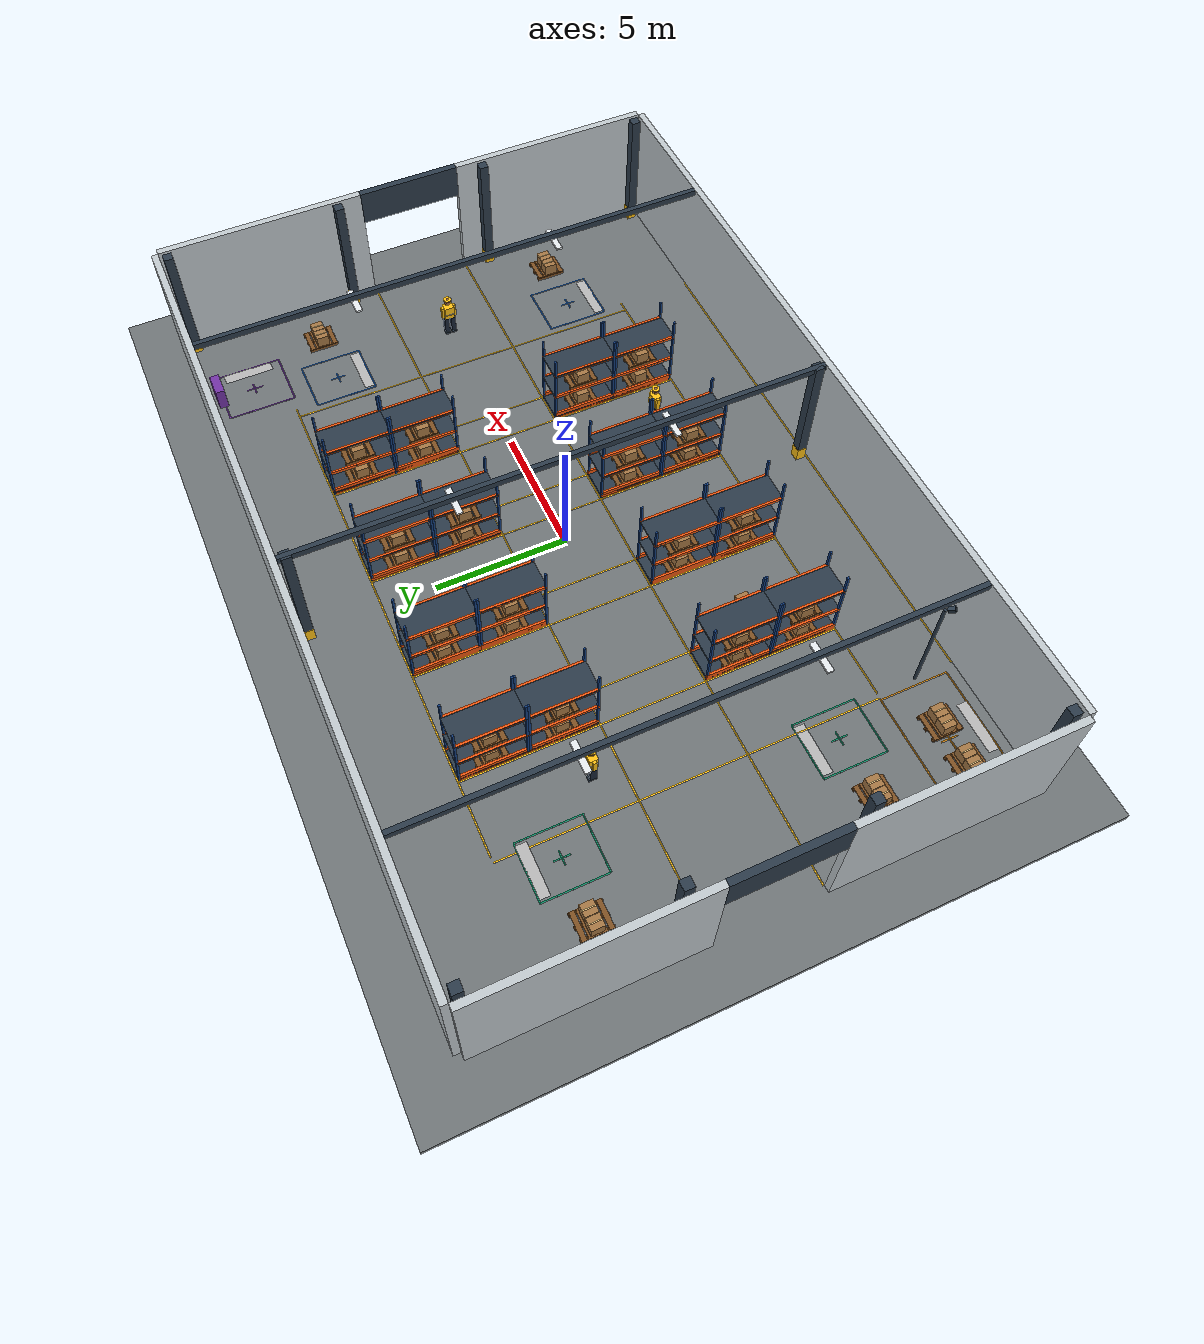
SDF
<?xml version="1.0"?>
<sdf version="1.9">
  <world name="warehouse">
    <gravity>0 0 -9.81</gravity>
    <physics name="physics" type="ignored">
      <max_step_size>0.001</max_step_size>
      <real_time_factor>1</real_time_factor>
    </physics>
    <plugin filename="gz-sim-physics-system" name="gz::sim::systems::Physics" />
    <plugin filename="gz-sim-user-commands-system" name="gz::sim::systems::UserCommands" />
    <plugin filename="gz-sim-scene-broadcaster-system" name="gz::sim::systems::SceneBroadcaster" />
    <plugin filename="gz-sim-sensors-system" name="gz::sim::systems::Sensors">
      <render_engine>ogre2</render_engine>
    </plugin>
    <plugin filename="gz-sim-imu-system" name="gz::sim::systems::Imu" />
    <plugin filename="gz-sim-contact-system" name="gz::sim::systems::Contact" />
    <scene>
      <ambient>0.42 0.43 0.45 1</ambient>
      <background>0.17 0.21 0.26 1</background>
      <shadows>true</shadows>
    </scene>
    <light name="daylight" type="directional">
      <pose>0 0 10 0 0 0</pose>
      <direction>-0.4 0.2 -1</direction>
      <diffuse>0.65 0.63 0.59 1</diffuse>
      <specular>0.1 0.1 0.1 1</specular>
      <cast_shadows>true</cast_shadows>
    </light>
    <light name="overhead_0" type="point">
      <pose>-10 -4 4.65 0 0 0</pose>
      <diffuse>0.55 0.57 0.6 1</diffuse>
      <cast_shadows>false</cast_shadows>
      <attenuation>
        <range>11</range>
        <constant>1</constant>
        <linear>0.035</linear>
        <quadratic>0.012</quadratic>
      </attenuation>
    </light>
    <light name="overhead_1" type="point">
      <pose>0 -4 4.65 0 0 0</pose>
      <diffuse>0.55 0.57 0.6 1</diffuse>
      <cast_shadows>false</cast_shadows>
      <attenuation>
        <range>11</range>
        <constant>1</constant>
        <linear>0.035</linear>
        <quadratic>0.012</quadratic>
      </attenuation>
    </light>
    <light name="overhead_2" type="point">
      <pose>10 -4 4.65 0 0 0</pose>
      <diffuse>0.55 0.57 0.6 1</diffuse>
      <cast_shadows>false</cast_shadows>
      <attenuation>
        <range>11</range>
        <constant>1</constant>
        <linear>0.035</linear>
        <quadratic>0.012</quadratic>
      </attenuation>
    </light>
    <light name="overhead_3" type="point">
      <pose>-10 4 4.65 0 0 0</pose>
      <diffuse>0.55 0.57 0.6 1</diffuse>
      <cast_shadows>false</cast_shadows>
      <attenuation>
        <range>11</range>
        <constant>1</constant>
        <linear>0.035</linear>
        <quadratic>0.012</quadratic>
      </attenuation>
    </light>
    <light name="overhead_4" type="point">
      <pose>0 4 4.65 0 0 0</pose>
      <diffuse>0.55 0.57 0.6 1</diffuse>
      <cast_shadows>false</cast_shadows>
      <attenuation>
        <range>11</range>
        <constant>1</constant>
        <linear>0.035</linear>
        <quadratic>0.012</quadratic>
      </attenuation>
    </light>
    <light name="overhead_5" type="point">
      <pose>10 4 4.65 0 0 0</pose>
      <diffuse>0.55 0.57 0.6 1</diffuse>
      <cast_shadows>false</cast_shadows>
      <attenuation>
        <range>11</range>
        <constant>1</constant>
        <linear>0.035</linear>
        <quadratic>0.012</quadratic>
      </attenuation>
    </light>
    <include>
      <uri>model://wh_building</uri>
      <name>warehouse_structure</name>
      <pose>0 0 0 0 0 0</pose>
    </include>
    <model name="warehouse_camera_01">
      <static>true</static>
      <pose>-10 -8.5 0 0 0 0</pose>
      <link name="mount">
        <visual name="mast_visual">
          <pose>0 0 2.2 0 0 0</pose>
          <geometry>
            <cylinder>
              <radius>0.055</radius>
              <length>4.4</length>
            </cylinder>
          </geometry>
          <material>
            <ambient>0.17 0.23 0.29 1</ambient>
            <diffuse>0.17 0.23 0.29 1</diffuse>
            <specular>0.06 0.06 0.06 1</specular>
          </material>
        </visual>
        <collision name="mast_collision">
          <pose>0 0 2.2 0 0 0</pose>
          <geometry>
            <cylinder>
              <radius>0.055</radius>
              <length>4.4</length>
            </cylinder>
          </geometry>
        </collision>
        <visual name="housing_visual">
          <pose>-0.125276387432 -0.142606210009 4.51121733507 0 0.53 0.85</pose>
          <geometry>
            <box>
              <size>0.24 0.16 0.16</size>
            </box>
          </geometry>
          <material>
            <ambient>0.17 0.23 0.29 1</ambient>
            <diffuse>0.17 0.23 0.29 1</diffuse>
            <specular>0.06 0.06 0.06 1</specular>
          </material>
        </visual>
        <collision name="housing_collision">
          <pose>-0.125276387432 -0.142606210009 4.51121733507 0 0.53 0.85</pose>
          <geometry>
            <box>
              <size>0.24 0.16 0.16</size>
            </box>
          </geometry>
        </collision>
        <sensor name="camera" type="camera">
          <pose>0 0 4.4 0 0.53 0.85</pose>
          <topic>/warehouse/camera_01/image</topic>
          <always_on>true</always_on>
          <update_rate>10</update_rate>
          <camera>
            <horizontal_fov>1.4</horizontal_fov>
            <image>
              <width>640</width>
              <height>480</height>
              <format>R8G8B8</format>
            </image>
            <clip>
              <near>0.1</near>
              <far>40</far>
            </clip>
            <optical_frame_id>warehouse_camera_01_optical_frame</optical_frame_id>
          </camera>
        </sensor>
      </link>
    </model>
    <model name="human_01">
      <static>false</static>
      <pose>-8.7 3 0 0 0 1.57079632679</pose>
      <link name="body">
        <inertial>
          <pose>0 0 0.25 0 0 0</pose>
          <mass>80</mass>
          <inertia>
            <ixx>12</ixx>
            <iyy>12</iyy>
            <izz>3.2</izz>
            <ixy>0</ixy>
            <ixz>0</ixz>
            <iyz>0</iyz>
          </inertia>
        </inertial>
        <collision name="body_collision">
          <pose>0 0 0.875 0 0 0</pose>
          <geometry>
            <cylinder>
              <radius>0.28</radius>
              <length>1.75</length>
            </cylinder>
          </geometry>
          <surface>
            <friction>
              <ode>
                <mu>0.05</mu>
                <mu2>0.05</mu2>
              </ode>
            </friction>
          </surface>
        </collision>
        <visual name="leg_-1_visual">
          <pose>0 -0.1344 0.4025 0 0 0</pose>
          <geometry>
            <box>
              <size>0.224 0.182 0.805</size>
            </box>
          </geometry>
          <material>
            <ambient>0.1 0.15 0.22 1</ambient>
            <diffuse>0.1 0.15 0.22 1</diffuse>
            <specular>0.06 0.06 0.06 1</specular>
          </material>
        </visual>
        <visual name="shoe_-1_visual">
          <pose>0.028 -0.1344 0.039375 0 0 0</pose>
          <geometry>
            <box>
              <size>0.308 0.196 0.07875</size>
            </box>
          </geometry>
          <material>
            <ambient>0.17 0.23 0.29 1</ambient>
            <diffuse>0.17 0.23 0.29 1</diffuse>
            <specular>0.06 0.06 0.06 1</specular>
          </material>
        </visual>
        <visual name="arm_-1_visual">
          <pose>0 -0.2324 1.085 0 0 0</pose>
          <geometry>
            <box>
              <size>0.1344 0.126 0.5425</size>
            </box>
          </geometry>
          <material>
            <ambient>1 0.76 0.08 1</ambient>
            <diffuse>1 0.76 0.08 1</diffuse>
            <specular>0.06 0.06 0.06 1</specular>
          </material>
        </visual>
        <visual name="leg_1_visual">
          <pose>0 0.1344 0.4025 0 0 0</pose>
          <geometry>
            <box>
              <size>0.224 0.182 0.805</size>
            </box>
          </geometry>
          <material>
            <ambient>0.1 0.15 0.22 1</ambient>
            <diffuse>0.1 0.15 0.22 1</diffuse>
            <specular>0.06 0.06 0.06 1</specular>
          </material>
        </visual>
        <visual name="shoe_1_visual">
          <pose>0.028 0.1344 0.039375 0 0 0</pose>
          <geometry>
            <box>
              <size>0.308 0.196 0.07875</size>
            </box>
          </geometry>
          <material>
            <ambient>0.17 0.23 0.29 1</ambient>
            <diffuse>0.17 0.23 0.29 1</diffuse>
            <specular>0.06 0.06 0.06 1</specular>
          </material>
        </visual>
        <visual name="arm_1_visual">
          <pose>0 0.2324 1.085 0 0 0</pose>
          <geometry>
            <box>
              <size>0.1344 0.126 0.5425</size>
            </box>
          </geometry>
          <material>
            <ambient>1 0.76 0.08 1</ambient>
            <diffuse>1 0.76 0.08 1</diffuse>
            <specular>0.06 0.06 0.06 1</specular>
          </material>
        </visual>
        <visual name="torso_visual">
          <pose>0 0 1.085 0 0 0</pose>
          <geometry>
            <box>
              <size>0.322 0.392 0.56</size>
            </box>
          </geometry>
          <material>
            <ambient>1 0.76 0.08 1</ambient>
            <diffuse>1 0.76 0.08 1</diffuse>
            <specular>0.06 0.06 0.06 1</specular>
          </material>
        </visual>
        <visual name="reflective_band_visual">
          <pose>0 0 1.015 0 0 0</pose>
          <geometry>
            <box>
              <size>0.3248 0.3948 0.049</size>
            </box>
          </geometry>
          <material>
            <ambient>0.91 0.93 0.94 1</ambient>
            <diffuse>0.91 0.93 0.94 1</diffuse>
            <specular>0.06 0.06 0.06 1</specular>
          </material>
        </visual>
        <visual name="head_visual">
          <pose>0 0 1.61 0 0 0</pose>
          <geometry>
            <sphere>
              <radius>0.14</radius>
            </sphere>
          </geometry>
          <material>
            <ambient>0.62 0.4 0.26 1</ambient>
            <diffuse>0.62 0.4 0.26 1</diffuse>
            <specular>0.06 0.06 0.06 1</specular>
          </material>
        </visual>
        <visual name="helmet_visual">
          <pose>0 0 1.7164 0 0 0</pose>
          <geometry>
            <cylinder>
              <radius>0.1484</radius>
              <length>0.042</length>
            </cylinder>
          </geometry>
          <material>
            <ambient>1 0.76 0.08 1</ambient>
            <diffuse>1 0.76 0.08 1</diffuse>
            <specular>0.06 0.06 0.06 1</specular>
          </material>
        </visual>
        <sensor name="human_01_contact" type="contact">
          <always_on>true</always_on>
          <update_rate>20</update_rate>
          <topic>/warehouse/contacts/human_01</topic>
          <contact>
            <collision>body_collision</collision>
            <topic>/warehouse/contacts/human_01</topic>
          </contact>
        </sensor>
      </link>
      <plugin filename="gz-sim-trajectory-follower-system" name="gz::sim::systems::TrajectoryFollower">
        <link_name>body</link_name>
        <loop>true</loop>
        <force>46</force>
        <torque>15</torque>
        <range_tolerance>0.3</range_tolerance>
        <bearing_tolerance>5</bearing_tolerance>
        <zero_vel_on_bearing_reached>true</zero_vel_on_bearing_reached>
        <waypoints>
          <waypoint>-8.7 6</waypoint>
          <waypoint>-8.7 3</waypoint>
        </waypoints>
      </plugin>
    </model>
    <model name="human_02">
      <static>false</static>
      <pose>3.9 -5.5 0 0 0 1.57079632679</pose>
      <link name="body">
        <inertial>
          <pose>0 0 0.25 0 0 0</pose>
          <mass>80</mass>
          <inertia>
            <ixx>12</ixx>
            <iyy>12</iyy>
            <izz>3.2</izz>
            <ixy>0</ixy>
            <ixz>0</ixz>
            <iyz>0</iyz>
          </inertia>
        </inertial>
        <collision name="body_collision">
          <pose>0 0 0.875 0 0 0</pose>
          <geometry>
            <cylinder>
              <radius>0.28</radius>
              <length>1.75</length>
            </cylinder>
          </geometry>
          <surface>
            <friction>
              <ode>
                <mu>0.05</mu>
                <mu2>0.05</mu2>
              </ode>
            </friction>
          </surface>
        </collision>
        <visual name="leg_-1_visual">
          <pose>0 -0.1344 0.4025 0 0 0</pose>
          <geometry>
            <box>
              <size>0.224 0.182 0.805</size>
            </box>
          </geometry>
          <material>
            <ambient>0.1 0.15 0.22 1</ambient>
            <diffuse>0.1 0.15 0.22 1</diffuse>
            <specular>0.06 0.06 0.06 1</specular>
          </material>
        </visual>
        <visual name="shoe_-1_visual">
          <pose>0.028 -0.1344 0.039375 0 0 0</pose>
          <geometry>
            <box>
              <size>0.308 0.196 0.07875</size>
            </box>
          </geometry>
          <material>
            <ambient>0.17 0.23 0.29 1</ambient>
            <diffuse>0.17 0.23 0.29 1</diffuse>
            <specular>0.06 0.06 0.06 1</specular>
          </material>
        </visual>
        <visual name="arm_-1_visual">
          <pose>0 -0.2324 1.085 0 0 0</pose>
          <geometry>
            <box>
              <size>0.1344 0.126 0.5425</size>
            </box>
          </geometry>
          <material>
            <ambient>1 0.76 0.08 1</ambient>
            <diffuse>1 0.76 0.08 1</diffuse>
            <specular>0.06 0.06 0.06 1</specular>
          </material>
        </visual>
        <visual name="leg_1_visual">
          <pose>0 0.1344 0.4025 0 0 0</pose>
          <geometry>
            <box>
              <size>0.224 0.182 0.805</size>
            </box>
          </geometry>
          <material>
            <ambient>0.1 0.15 0.22 1</ambient>
            <diffuse>0.1 0.15 0.22 1</diffuse>
            <specular>0.06 0.06 0.06 1</specular>
          </material>
        </visual>
        <visual name="shoe_1_visual">
          <pose>0.028 0.1344 0.039375 0 0 0</pose>
          <geometry>
            <box>
              <size>0.308 0.196 0.07875</size>
            </box>
          </geometry>
          <material>
            <ambient>0.17 0.23 0.29 1</ambient>
            <diffuse>0.17 0.23 0.29 1</diffuse>
            <specular>0.06 0.06 0.06 1</specular>
          </material>
        </visual>
        <visual name="arm_1_visual">
          <pose>0 0.2324 1.085 0 0 0</pose>
          <geometry>
            <box>
              <size>0.1344 0.126 0.5425</size>
            </box>
          </geometry>
          <material>
            <ambient>1 0.76 0.08 1</ambient>
            <diffuse>1 0.76 0.08 1</diffuse>
            <specular>0.06 0.06 0.06 1</specular>
          </material>
        </visual>
        <visual name="torso_visual">
          <pose>0 0 1.085 0 0 0</pose>
          <geometry>
            <box>
              <size>0.322 0.392 0.56</size>
            </box>
          </geometry>
          <material>
            <ambient>1 0.76 0.08 1</ambient>
            <diffuse>1 0.76 0.08 1</diffuse>
            <specular>0.06 0.06 0.06 1</specular>
          </material>
        </visual>
        <visual name="reflective_band_visual">
          <pose>0 0 1.015 0 0 0</pose>
          <geometry>
            <box>
              <size>0.3248 0.3948 0.049</size>
            </box>
          </geometry>
          <material>
            <ambient>0.91 0.93 0.94 1</ambient>
            <diffuse>0.91 0.93 0.94 1</diffuse>
            <specular>0.06 0.06 0.06 1</specular>
          </material>
        </visual>
        <visual name="head_visual">
          <pose>0 0 1.61 0 0 0</pose>
          <geometry>
            <sphere>
              <radius>0.14</radius>
            </sphere>
          </geometry>
          <material>
            <ambient>0.62 0.4 0.26 1</ambient>
            <diffuse>0.62 0.4 0.26 1</diffuse>
            <specular>0.06 0.06 0.06 1</specular>
          </material>
        </visual>
        <visual name="helmet_visual">
          <pose>0 0 1.7164 0 0 0</pose>
          <geometry>
            <cylinder>
              <radius>0.1484</radius>
              <length>0.042</length>
            </cylinder>
          </geometry>
          <material>
            <ambient>1 0.76 0.08 1</ambient>
            <diffuse>1 0.76 0.08 1</diffuse>
            <specular>0.06 0.06 0.06 1</specular>
          </material>
        </visual>
        <sensor name="human_02_contact" type="contact">
          <always_on>true</always_on>
          <update_rate>20</update_rate>
          <topic>/warehouse/contacts/human_02</topic>
          <contact>
            <collision>body_collision</collision>
            <topic>/warehouse/contacts/human_02</topic>
          </contact>
        </sensor>
      </link>
      <plugin filename="gz-sim-trajectory-follower-system" name="gz::sim::systems::TrajectoryFollower">
        <link_name>body</link_name>
        <loop>true</loop>
        <force>46</force>
        <torque>15</torque>
        <range_tolerance>0.3</range_tolerance>
        <bearing_tolerance>5</bearing_tolerance>
        <zero_vel_on_bearing_reached>true</zero_vel_on_bearing_reached>
        <waypoints>
          <waypoint>3.9 5.5</waypoint>
          <waypoint>3.9 -5.5</waypoint>
        </waypoints>
      </plugin>
    </model>
    <model name="human_03">
      <static>true</static>
      <pose>11.5 0 0 0 0 3.14159265359</pose>
      <link name="body">
        <inertial>
          <pose>0 0 0.25 0 0 0</pose>
          <mass>80</mass>
          <inertia>
            <ixx>12</ixx>
            <iyy>12</iyy>
            <izz>3.2</izz>
            <ixy>0</ixy>
            <ixz>0</ixz>
            <iyz>0</iyz>
          </inertia>
        </inertial>
        <collision name="body_collision">
          <pose>0 0 0.875 0 0 0</pose>
          <geometry>
            <cylinder>
              <radius>0.28</radius>
              <length>1.75</length>
            </cylinder>
          </geometry>
          <surface>
            <friction>
              <ode>
                <mu>0.05</mu>
                <mu2>0.05</mu2>
              </ode>
            </friction>
          </surface>
        </collision>
        <visual name="leg_-1_visual">
          <pose>0 -0.1344 0.4025 0 0 0</pose>
          <geometry>
            <box>
              <size>0.224 0.182 0.805</size>
            </box>
          </geometry>
          <material>
            <ambient>0.1 0.15 0.22 1</ambient>
            <diffuse>0.1 0.15 0.22 1</diffuse>
            <specular>0.06 0.06 0.06 1</specular>
          </material>
        </visual>
        <visual name="shoe_-1_visual">
          <pose>0.028 -0.1344 0.039375 0 0 0</pose>
          <geometry>
            <box>
              <size>0.308 0.196 0.07875</size>
            </box>
          </geometry>
          <material>
            <ambient>0.17 0.23 0.29 1</ambient>
            <diffuse>0.17 0.23 0.29 1</diffuse>
            <specular>0.06 0.06 0.06 1</specular>
          </material>
        </visual>
        <visual name="arm_-1_visual">
          <pose>0 -0.2324 1.085 0 0 0</pose>
          <geometry>
            <box>
              <size>0.1344 0.126 0.5425</size>
            </box>
          </geometry>
          <material>
            <ambient>1 0.76 0.08 1</ambient>
            <diffuse>1 0.76 0.08 1</diffuse>
            <specular>0.06 0.06 0.06 1</specular>
          </material>
        </visual>
        <visual name="leg_1_visual">
          <pose>0 0.1344 0.4025 0 0 0</pose>
          <geometry>
            <box>
              <size>0.224 0.182 0.805</size>
            </box>
          </geometry>
          <material>
            <ambient>0.1 0.15 0.22 1</ambient>
            <diffuse>0.1 0.15 0.22 1</diffuse>
            <specular>0.06 0.06 0.06 1</specular>
          </material>
        </visual>
        <visual name="shoe_1_visual">
          <pose>0.028 0.1344 0.039375 0 0 0</pose>
          <geometry>
            <box>
              <size>0.308 0.196 0.07875</size>
            </box>
          </geometry>
          <material>
            <ambient>0.17 0.23 0.29 1</ambient>
            <diffuse>0.17 0.23 0.29 1</diffuse>
            <specular>0.06 0.06 0.06 1</specular>
          </material>
        </visual>
        <visual name="arm_1_visual">
          <pose>0 0.2324 1.085 0 0 0</pose>
          <geometry>
            <box>
              <size>0.1344 0.126 0.5425</size>
            </box>
          </geometry>
          <material>
            <ambient>1 0.76 0.08 1</ambient>
            <diffuse>1 0.76 0.08 1</diffuse>
            <specular>0.06 0.06 0.06 1</specular>
          </material>
        </visual>
        <visual name="torso_visual">
          <pose>0 0 1.085 0 0 0</pose>
          <geometry>
            <box>
              <size>0.322 0.392 0.56</size>
            </box>
          </geometry>
          <material>
            <ambient>1 0.76 0.08 1</ambient>
            <diffuse>1 0.76 0.08 1</diffuse>
            <specular>0.06 0.06 0.06 1</specular>
          </material>
        </visual>
        <visual name="reflective_band_visual">
          <pose>0 0 1.015 0 0 0</pose>
          <geometry>
            <box>
              <size>0.3248 0.3948 0.049</size>
            </box>
          </geometry>
          <material>
            <ambient>0.91 0.93 0.94 1</ambient>
            <diffuse>0.91 0.93 0.94 1</diffuse>
            <specular>0.06 0.06 0.06 1</specular>
          </material>
        </visual>
        <visual name="head_visual">
          <pose>0 0 1.61 0 0 0</pose>
          <geometry>
            <sphere>
              <radius>0.14</radius>
            </sphere>
          </geometry>
          <material>
            <ambient>0.62 0.4 0.26 1</ambient>
            <diffuse>0.62 0.4 0.26 1</diffuse>
            <specular>0.06 0.06 0.06 1</specular>
          </material>
        </visual>
        <visual name="helmet_visual">
          <pose>0 0 1.7164 0 0 0</pose>
          <geometry>
            <cylinder>
              <radius>0.1484</radius>
              <length>0.042</length>
            </cylinder>
          </geometry>
          <material>
            <ambient>1 0.76 0.08 1</ambient>
            <diffuse>1 0.76 0.08 1</diffuse>
            <specular>0.06 0.06 0.06 1</specular>
          </material>
        </visual>
        <sensor name="human_03_contact" type="contact">
          <always_on>true</always_on>
          <update_rate>20</update_rate>
          <topic>/warehouse/contacts/human_03</topic>
          <contact>
            <collision>body_collision</collision>
            <topic>/warehouse/contacts/human_03</topic>
          </contact>
        </sensor>
      </link>
    </model>
    <include>
      <uri>model://wh_loaded_pallet</uri>
      <name>aisle_pallet</name>
      <pose>-5.35 -4.5 0 0 0 0</pose>
    </include>
  </world>
</sdf>

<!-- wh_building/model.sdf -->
<sdf version="1.9">
  <model name="wh_building">
    <static>true</static>
    <link name="structure">
      <visual name="floor_visual">
        <pose>0 0 -0.1 0 0 0</pose>
        <geometry>
          <box>
            <size>34 24 0.2</size>
          </box>
        </geometry>
        <material>
          <ambient>0.44 0.46 0.47 1</ambient>
          <diffuse>0.44 0.46 0.47 1</diffuse>
          <specular>0.06 0.06 0.06 1</specular>
        </material>
      </visual>
      <collision name="floor_collision">
        <pose>0 0 -0.1 0 0 0</pose>
        <geometry>
          <box>
            <size>34 24 0.2</size>
          </box>
        </geometry>
      </collision>
      <visual name="west_wall_0_visual">
        <pose>-15.125 -6 2.5 0 0 0</pose>
        <geometry>
          <box>
            <size>0.25 8 5</size>
          </box>
        </geometry>
        <material>
          <ambient>0.76 0.79 0.81 1</ambient>
          <diffuse>0.76 0.79 0.81 1</diffuse>
          <specular>0.06 0.06 0.06 1</specular>
        </material>
      </visual>
      <collision name="west_wall_0_collision">
        <pose>-15.125 -6 2.5 0 0 0</pose>
        <geometry>
          <box>
            <size>0.25 8 5</size>
          </box>
        </geometry>
      </collision>
      <visual name="receiving_door_lintel_visual">
        <pose>-15.125 0 4.3 0 0 0</pose>
        <geometry>
          <box>
            <size>0.25 4 1.4</size>
          </box>
        </geometry>
        <material>
          <ambient>0.17 0.23 0.29 1</ambient>
          <diffuse>0.17 0.23 0.29 1</diffuse>
          <specular>0.06 0.06 0.06 1</specular>
        </material>
      </visual>
      <collision name="receiving_door_lintel_collision">
        <pose>-15.125 0 4.3 0 0 0</pose>
        <geometry>
          <box>
            <size>0.25 4 1.4</size>
          </box>
        </geometry>
      </collision>
      <visual name="west_wall_1_visual">
        <pose>-15.125 6 2.5 0 0 0</pose>
        <geometry>
          <box>
            <size>0.25 8 5</size>
          </box>
        </geometry>
        <material>
          <ambient>0.76 0.79 0.81 1</ambient>
          <diffuse>0.76 0.79 0.81 1</diffuse>
          <specular>0.06 0.06 0.06 1</specular>
        </material>
      </visual>
      <collision name="west_wall_1_collision">
        <pose>-15.125 6 2.5 0 0 0</pose>
        <geometry>
          <box>
            <size>0.25 8 5</size>
          </box>
        </geometry>
      </collision>
      <visual name="east_wall_0_visual">
        <pose>15.125 -6 2.5 0 0 0</pose>
        <geometry>
          <box>
            <size>0.25 8 5</size>
          </box>
        </geometry>
        <material>
          <ambient>0.76 0.79 0.81 1</ambient>
          <diffuse>0.76 0.79 0.81 1</diffuse>
          <specular>0.06 0.06 0.06 1</specular>
        </material>
      </visual>
      <collision name="east_wall_0_collision">
        <pose>15.125 -6 2.5 0 0 0</pose>
        <geometry>
          <box>
            <size>0.25 8 5</size>
          </box>
        </geometry>
      </collision>
      <visual name="dispatch_door_lintel_visual">
        <pose>15.125 0 4.3 0 0 0</pose>
        <geometry>
          <box>
            <size>0.25 4 1.4</size>
          </box>
        </geometry>
        <material>
          <ambient>0.17 0.23 0.29 1</ambient>
          <diffuse>0.17 0.23 0.29 1</diffuse>
          <specular>0.06 0.06 0.06 1</specular>
        </material>
      </visual>
      <collision name="dispatch_door_lintel_collision">
        <pose>15.125 0 4.3 0 0 0</pose>
        <geometry>
          <box>
            <size>0.25 4 1.4</size>
          </box>
        </geometry>
      </collision>
      <visual name="east_wall_1_visual">
        <pose>15.125 6 2.5 0 0 0</pose>
        <geometry>
          <box>
            <size>0.25 8 5</size>
          </box>
        </geometry>
        <material>
          <ambient>0.76 0.79 0.81 1</ambient>
          <diffuse>0.76 0.79 0.81 1</diffuse>
          <specular>0.06 0.06 0.06 1</specular>
        </material>
      </visual>
      <collision name="east_wall_1_collision">
        <pose>15.125 6 2.5 0 0 0</pose>
        <geometry>
          <box>
            <size>0.25 8 5</size>
          </box>
        </geometry>
      </collision>
      <visual name="north_wall_0_visual">
        <pose>0 10.125 2.5 0 0 0</pose>
        <geometry>
          <box>
            <size>30 0.25 5</size>
          </box>
        </geometry>
        <material>
          <ambient>0.76 0.79 0.81 1</ambient>
          <diffuse>0.76 0.79 0.81 1</diffuse>
          <specular>0.06 0.06 0.06 1</specular>
        </material>
      </visual>
      <collision name="north_wall_0_collision">
        <pose>0 10.125 2.5 0 0 0</pose>
        <geometry>
          <box>
            <size>30 0.25 5</size>
          </box>
        </geometry>
      </collision>
      <visual name="south_wall_0_visual">
        <pose>0 -10.125 2.5 0 0 0</pose>
        <geometry>
          <box>
            <size>30 0.25 5</size>
          </box>
        </geometry>
        <material>
          <ambient>0.76 0.79 0.81 1</ambient>
          <diffuse>0.76 0.79 0.81 1</diffuse>
          <specular>0.06 0.06 0.06 1</specular>
        </material>
      </visual>
      <collision name="south_wall_0_collision">
        <pose>0 -10.125 2.5 0 0 0</pose>
        <geometry>
          <box>
            <size>30 0.25 5</size>
          </box>
        </geometry>
      </collision>
      <visual name="pillar_00_visual">
        <pose>-14.7 -9.7 2.5 0 0 0</pose>
        <geometry>
          <box>
            <size>0.35 0.35 5</size>
          </box>
        </geometry>
        <material>
          <ambient>0.17 0.23 0.29 1</ambient>
          <diffuse>0.17 0.23 0.29 1</diffuse>
          <specular>0.06 0.06 0.06 1</specular>
        </material>
      </visual>
      <collision name="pillar_00_collision">
        <pose>-14.7 -9.7 2.5 0 0 0</pose>
        <geometry>
          <box>
            <size>0.35 0.35 5</size>
          </box>
        </geometry>
      </collision>
      <visual name="pillar_guard_00_visual">
        <pose>-14.7 -9.7 0.275 0 0 0</pose>
        <geometry>
          <box>
            <size>0.365 0.365 0.55</size>
          </box>
        </geometry>
        <material>
          <ambient>1 0.76 0.08 1</ambient>
          <diffuse>1 0.76 0.08 1</diffuse>
          <specular>0.06 0.06 0.06 1</specular>
        </material>
      </visual>
      <visual name="pillar_01_visual">
        <pose>-14.7 -3 2.5 0 0 0</pose>
        <geometry>
          <box>
            <size>0.35 0.35 5</size>
          </box>
        </geometry>
        <material>
          <ambient>0.17 0.23 0.29 1</ambient>
          <diffuse>0.17 0.23 0.29 1</diffuse>
          <specular>0.06 0.06 0.06 1</specular>
        </material>
      </visual>
      <collision name="pillar_01_collision">
        <pose>-14.7 -3 2.5 0 0 0</pose>
        <geometry>
          <box>
            <size>0.35 0.35 5</size>
          </box>
        </geometry>
      </collision>
      <visual name="pillar_guard_01_visual">
        <pose>-14.7 -3 0.275 0 0 0</pose>
        <geometry>
          <box>
            <size>0.365 0.365 0.55</size>
          </box>
        </geometry>
        <material>
          <ambient>1 0.76 0.08 1</ambient>
          <diffuse>1 0.76 0.08 1</diffuse>
          <specular>0.06 0.06 0.06 1</specular>
        </material>
      </visual>
      <visual name="pillar_02_visual">
        <pose>-14.7 3 2.5 0 0 0</pose>
        <geometry>
          <box>
            <size>0.35 0.35 5</size>
          </box>
        </geometry>
        <material>
          <ambient>0.17 0.23 0.29 1</ambient>
          <diffuse>0.17 0.23 0.29 1</diffuse>
          <specular>0.06 0.06 0.06 1</specular>
        </material>
      </visual>
      <collision name="pillar_02_collision">
        <pose>-14.7 3 2.5 0 0 0</pose>
        <geometry>
          <box>
            <size>0.35 0.35 5</size>
          </box>
        </geometry>
      </collision>
      <visual name="pillar_guard_02_visual">
        <pose>-14.7 3 0.275 0 0 0</pose>
        <geometry>
          <box>
            <size>0.365 0.365 0.55</size>
          </box>
        </geometry>
        <material>
          <ambient>1 0.76 0.08 1</ambient>
          <diffuse>1 0.76 0.08 1</diffuse>
          <specular>0.06 0.06 0.06 1</specular>
        </material>
      </visual>
      <visual name="pillar_03_visual">
        <pose>-14.7 9.7 2.5 0 0 0</pose>
        <geometry>
          <box>
            <size>0.35 0.35 5</size>
          </box>
        </geometry>
        <material>
          <ambient>0.17 0.23 0.29 1</ambient>
          <diffuse>0.17 0.23 0.29 1</diffuse>
          <specular>0.06 0.06 0.06 1</specular>
        </material>
      </visual>
      <collision name="pillar_03_collision">
        <pose>-14.7 9.7 2.5 0 0 0</pose>
        <geometry>
          <box>
            <size>0.35 0.35 5</size>
          </box>
        </geometry>
      </collision>
      <visual name="pillar_guard_03_visual">
        <pose>-14.7 9.7 0.275 0 0 0</pose>
        <geometry>
          <box>
            <size>0.365 0.365 0.55</size>
          </box>
        </geometry>
        <material>
          <ambient>1 0.76 0.08 1</ambient>
          <diffuse>1 0.76 0.08 1</diffuse>
          <specular>0.06 0.06 0.06 1</specular>
        </material>
      </visual>
      <visual name="pillar_04_visual">
        <pose>0 -9.7 2.5 0 0 0</pose>
        <geometry>
          <box>
            <size>0.35 0.35 5</size>
          </box>
        </geometry>
        <material>
          <ambient>0.17 0.23 0.29 1</ambient>
          <diffuse>0.17 0.23 0.29 1</diffuse>
          <specular>0.06 0.06 0.06 1</specular>
        </material>
      </visual>
      <collision name="pillar_04_collision">
        <pose>0 -9.7 2.5 0 0 0</pose>
        <geometry>
          <box>
            <size>0.35 0.35 5</size>
          </box>
        </geometry>
      </collision>
      <visual name="pillar_guard_04_visual">
        <pose>0 -9.7 0.275 0 0 0</pose>
        <geometry>
          <box>
            <size>0.365 0.365 0.55</size>
          </box>
        </geometry>
        <material>
          <ambient>1 0.76 0.08 1</ambient>
          <diffuse>1 0.76 0.08 1</diffuse>
          <specular>0.06 0.06 0.06 1</specular>
        </material>
      </visual>
      <visual name="pillar_05_visual">
        <pose>0 9.7 2.5 0 0 0</pose>
        <geometry>
          <box>
            <size>0.35 0.35 5</size>
          </box>
        </geometry>
        <material>
          <ambient>0.17 0.23 0.29 1</ambient>
          <diffuse>0.17 0.23 0.29 1</diffuse>
          <specular>0.06 0.06 0.06 1</specular>
        </material>
      </visual>
      <collision name="pillar_05_collision">
        <pose>0 9.7 2.5 0 0 0</pose>
        <geometry>
          <box>
            <size>0.35 0.35 5</size>
          </box>
        </geometry>
      </collision>
      <visual name="pillar_guard_05_visual">
        <pose>0 9.7 0.275 0 0 0</pose>
        <geometry>
          <box>
            <size>0.365 0.365 0.55</size>
          </box>
        </geometry>
        <material>
          <ambient>1 0.76 0.08 1</ambient>
          <diffuse>1 0.76 0.08 1</diffuse>
          <specular>0.06 0.06 0.06 1</specular>
        </material>
      </visual>
      <visual name="pillar_06_visual">
        <pose>14.7 -9.7 2.5 0 0 0</pose>
        <geometry>
          <box>
            <size>0.35 0.35 5</size>
          </box>
        </geometry>
        <material>
          <ambient>0.17 0.23 0.29 1</ambient>
          <diffuse>0.17 0.23 0.29 1</diffuse>
          <specular>0.06 0.06 0.06 1</specular>
        </material>
      </visual>
      <collision name="pillar_06_collision">
        <pose>14.7 -9.7 2.5 0 0 0</pose>
        <geometry>
          <box>
            <size>0.35 0.35 5</size>
          </box>
        </geometry>
      </collision>
      <visual name="pillar_guard_06_visual">
        <pose>14.7 -9.7 0.275 0 0 0</pose>
        <geometry>
          <box>
            <size>0.365 0.365 0.55</size>
          </box>
        </geometry>
        <material>
          <ambient>1 0.76 0.08 1</ambient>
          <diffuse>1 0.76 0.08 1</diffuse>
          <specular>0.06 0.06 0.06 1</specular>
        </material>
      </visual>
      <visual name="pillar_07_visual">
        <pose>14.7 -3 2.5 0 0 0</pose>
        <geometry>
          <box>
            <size>0.35 0.35 5</size>
          </box>
        </geometry>
        <material>
          <ambient>0.17 0.23 0.29 1</ambient>
          <diffuse>0.17 0.23 0.29 1</diffuse>
          <specular>0.06 0.06 0.06 1</specular>
        </material>
      </visual>
      <collision name="pillar_07_collision">
        <pose>14.7 -3 2.5 0 0 0</pose>
        <geometry>
          <box>
            <size>0.35 0.35 5</size>
          </box>
        </geometry>
      </collision>
      <visual name="pillar_guard_07_visual">
        <pose>14.7 -3 0.275 0 0 0</pose>
        <geometry>
          <box>
            <size>0.365 0.365 0.55</size>
          </box>
        </geometry>
        <material>
          <ambient>1 0.76 0.08 1</ambient>
          <diffuse>1 0.76 0.08 1</diffuse>
          <specular>0.06 0.06 0.06 1</specular>
        </material>
      </visual>
      <visual name="pillar_08_visual">
        <pose>14.7 3 2.5 0 0 0</pose>
        <geometry>
          <box>
            <size>0.35 0.35 5</size>
          </box>
        </geometry>
        <material>
          <ambient>0.17 0.23 0.29 1</ambient>
          <diffuse>0.17 0.23 0.29 1</diffuse>
          <specular>0.06 0.06 0.06 1</specular>
        </material>
      </visual>
      <collision name="pillar_08_collision">
        <pose>14.7 3 2.5 0 0 0</pose>
        <geometry>
          <box>
            <size>0.35 0.35 5</size>
          </box>
        </geometry>
      </collision>
      <visual name="pillar_guard_08_visual">
        <pose>14.7 3 0.275 0 0 0</pose>
        <geometry>
          <box>
            <size>0.365 0.365 0.55</size>
          </box>
        </geometry>
        <material>
          <ambient>1 0.76 0.08 1</ambient>
          <diffuse>1 0.76 0.08 1</diffuse>
          <specular>0.06 0.06 0.06 1</specular>
        </material>
      </visual>
      <visual name="pillar_09_visual">
        <pose>14.7 9.7 2.5 0 0 0</pose>
        <geometry>
          <box>
            <size>0.35 0.35 5</size>
          </box>
        </geometry>
        <material>
          <ambient>0.17 0.23 0.29 1</ambient>
          <diffuse>0.17 0.23 0.29 1</diffuse>
          <specular>0.06 0.06 0.06 1</specular>
        </material>
      </visual>
      <collision name="pillar_09_collision">
        <pose>14.7 9.7 2.5 0 0 0</pose>
        <geometry>
          <box>
            <size>0.35 0.35 5</size>
          </box>
        </geometry>
      </collision>
      <visual name="pillar_guard_09_visual">
        <pose>14.7 9.7 0.275 0 0 0</pose>
        <geometry>
          <box>
            <size>0.365 0.365 0.55</size>
          </box>
        </geometry>
        <material>
          <ambient>1 0.76 0.08 1</ambient>
          <diffuse>1 0.76 0.08 1</diffuse>
          <specular>0.06 0.06 0.06 1</specular>
        </material>
      </visual>
      <visual name="roof_beam_0_visual">
        <pose>-10 0 4.88 0 0 0</pose>
        <geometry>
          <box>
            <size>0.18 20 0.24</size>
          </box>
        </geometry>
        <material>
          <ambient>0.17 0.23 0.29 1</ambient>
          <diffuse>0.17 0.23 0.29 1</diffuse>
          <specular>0.06 0.06 0.06 1</specular>
        </material>
      </visual>
      <collision name="roof_beam_0_collision">
        <pose>-10 0 4.88 0 0 0</pose>
        <geometry>
          <box>
            <size>0.18 20 0.24</size>
          </box>
        </geometry>
      </collision>
      <visual name="roof_beam_1_visual">
        <pose>0 0 4.88 0 0 0</pose>
        <geometry>
          <box>
            <size>0.18 20 0.24</size>
          </box>
        </geometry>
        <material>
          <ambient>0.17 0.23 0.29 1</ambient>
          <diffuse>0.17 0.23 0.29 1</diffuse>
          <specular>0.06 0.06 0.06 1</specular>
        </material>
      </visual>
      <collision name="roof_beam_1_collision">
        <pose>0 0 4.88 0 0 0</pose>
        <geometry>
          <box>
            <size>0.18 20 0.24</size>
          </box>
        </geometry>
      </collision>
      <visual name="roof_beam_2_visual">
        <pose>10 0 4.88 0 0 0</pose>
        <geometry>
          <box>
            <size>0.18 20 0.24</size>
          </box>
        </geometry>
        <material>
          <ambient>0.17 0.23 0.29 1</ambient>
          <diffuse>0.17 0.23 0.29 1</diffuse>
          <specular>0.06 0.06 0.06 1</specular>
        </material>
      </visual>
      <collision name="roof_beam_2_collision">
        <pose>10 0 4.88 0 0 0</pose>
        <geometry>
          <box>
            <size>0.18 20 0.24</size>
          </box>
        </geometry>
      </collision>
      <visual name="aisle_0_-1_visual">
        <pose>0 -1.975 0.0015 0 0 0</pose>
        <geometry>
          <box>
            <size>30 0.05 0.003</size>
          </box>
        </geometry>
        <material>
          <ambient>1 0.76 0.08 1</ambient>
          <diffuse>1 0.76 0.08 1</diffuse>
          <specular>0.06 0.06 0.06 1</specular>
        </material>
      </visual>
      <visual name="aisle_0_1_visual">
        <pose>0 1.975 0.0015 0 0 0</pose>
        <geometry>
          <box>
            <size>30 0.05 0.003</size>
          </box>
        </geometry>
        <material>
          <ambient>1 0.76 0.08 1</ambient>
          <diffuse>1 0.76 0.08 1</diffuse>
          <specular>0.06 0.06 0.06 1</specular>
        </material>
      </visual>
      <visual name="aisle_1_-1_visual">
        <pose>0 7.025 0.0015 0 0 0</pose>
        <geometry>
          <box>
            <size>20 0.05 0.003</size>
          </box>
        </geometry>
        <material>
          <ambient>1 0.76 0.08 1</ambient>
          <diffuse>1 0.76 0.08 1</diffuse>
          <specular>0.06 0.06 0.06 1</specular>
        </material>
      </visual>
      <visual name="aisle_1_1_visual">
        <pose>0 9.975 0.0015 0 0 0</pose>
        <geometry>
          <box>
            <size>20 0.05 0.003</size>
          </box>
        </geometry>
        <material>
          <ambient>1 0.76 0.08 1</ambient>
          <diffuse>1 0.76 0.08 1</diffuse>
          <specular>0.06 0.06 0.06 1</specular>
        </material>
      </visual>
      <visual name="aisle_2_-1_visual">
        <pose>0 -9.975 0.0015 0 0 0</pose>
        <geometry>
          <box>
            <size>20 0.05 0.003</size>
          </box>
        </geometry>
        <material>
          <ambient>1 0.76 0.08 1</ambient>
          <diffuse>1 0.76 0.08 1</diffuse>
          <specular>0.06 0.06 0.06 1</specular>
        </material>
      </visual>
      <visual name="aisle_2_1_visual">
        <pose>0 -7.025 0.0015 0 0 0</pose>
        <geometry>
          <box>
            <size>20 0.05 0.003</size>
          </box>
        </geometry>
        <material>
          <ambient>1 0.76 0.08 1</ambient>
          <diffuse>1 0.76 0.08 1</diffuse>
          <specular>0.06 0.06 0.06 1</specular>
        </material>
      </visual>
      <visual name="aisle_3_-1_visual">
        <pose>-5.975 0 0.0015 0 0 0</pose>
        <geometry>
          <box>
            <size>0.05 14 0.003</size>
          </box>
        </geometry>
        <material>
          <ambient>1 0.76 0.08 1</ambient>
          <diffuse>1 0.76 0.08 1</diffuse>
          <specular>0.06 0.06 0.06 1</specular>
        </material>
      </visual>
      <visual name="aisle_3_1_visual">
        <pose>-3.025 0 0.0015 0 0 0</pose>
        <geometry>
          <box>
            <size>0.05 14 0.003</size>
          </box>
        </geometry>
        <material>
          <ambient>1 0.76 0.08 1</ambient>
          <diffuse>1 0.76 0.08 1</diffuse>
          <specular>0.06 0.06 0.06 1</specular>
        </material>
      </visual>
      <visual name="aisle_4_-1_visual">
        <pose>-1.775 0 0.0015 0 0 0</pose>
        <geometry>
          <box>
            <size>0.05 14 0.003</size>
          </box>
        </geometry>
        <material>
          <ambient>1 0.76 0.08 1</ambient>
          <diffuse>1 0.76 0.08 1</diffuse>
          <specular>0.06 0.06 0.06 1</specular>
        </material>
      </visual>
      <visual name="aisle_4_1_visual">
        <pose>1.175 0 0.0015 0 0 0</pose>
        <geometry>
          <box>
            <size>0.05 14 0.003</size>
          </box>
        </geometry>
        <material>
          <ambient>1 0.76 0.08 1</ambient>
          <diffuse>1 0.76 0.08 1</diffuse>
          <specular>0.06 0.06 0.06 1</specular>
        </material>
      </visual>
      <visual name="aisle_5_-1_visual">
        <pose>2.425 0 0.0015 0 0 0</pose>
        <geometry>
          <box>
            <size>0.05 14 0.003</size>
          </box>
        </geometry>
        <material>
          <ambient>1 0.76 0.08 1</ambient>
          <diffuse>1 0.76 0.08 1</diffuse>
          <specular>0.06 0.06 0.06 1</specular>
        </material>
      </visual>
      <visual name="aisle_5_1_visual">
        <pose>5.375 0 0.0015 0 0 0</pose>
        <geometry>
          <box>
            <size>0.05 14 0.003</size>
          </box>
        </geometry>
        <material>
          <ambient>1 0.76 0.08 1</ambient>
          <diffuse>1 0.76 0.08 1</diffuse>
          <specular>0.06 0.06 0.06 1</specular>
        </material>
      </visual>
      <visual name="aisle_6_-1_visual">
        <pose>-10.175 0 0.0015 0 0 0</pose>
        <geometry>
          <box>
            <size>0.05 14 0.003</size>
          </box>
        </geometry>
        <material>
          <ambient>1 0.76 0.08 1</ambient>
          <diffuse>1 0.76 0.08 1</diffuse>
          <specular>0.06 0.06 0.06 1</specular>
        </material>
      </visual>
      <visual name="aisle_6_1_visual">
        <pose>-7.225 0 0.0015 0 0 0</pose>
        <geometry>
          <box>
            <size>0.05 14 0.003</size>
          </box>
        </geometry>
        <material>
          <ambient>1 0.76 0.08 1</ambient>
          <diffuse>1 0.76 0.08 1</diffuse>
          <specular>0.06 0.06 0.06 1</specular>
        </material>
      </visual>
      <visual name="aisle_7_-1_visual">
        <pose>6.625 0 0.0015 0 0 0</pose>
        <geometry>
          <box>
            <size>0.05 14 0.003</size>
          </box>
        </geometry>
        <material>
          <ambient>1 0.76 0.08 1</ambient>
          <diffuse>1 0.76 0.08 1</diffuse>
          <specular>0.06 0.06 0.06 1</specular>
        </material>
      </visual>
      <visual name="aisle_7_1_visual">
        <pose>9.575 0 0.0015 0 0 0</pose>
        <geometry>
          <box>
            <size>0.05 14 0.003</size>
          </box>
        </geometry>
        <material>
          <ambient>1 0.76 0.08 1</ambient>
          <diffuse>1 0.76 0.08 1</diffuse>
          <specular>0.06 0.06 0.06 1</specular>
        </material>
      </visual>
      <sensor name="south_wall_contact" type="contact">
        <always_on>true</always_on>
        <update_rate>20</update_rate>
        <topic>/warehouse/contacts/wall</topic>
        <contact>
          <collision>south_wall_0_collision</collision>
          <topic>/warehouse/contacts/wall</topic>
        </contact>
      </sensor>
      <visual name="charger_visual">
        <pose>11.7 9.55 0.45 0 0 0</pose>
        <geometry>
          <box>
            <size>0.9 0.35 0.9</size>
          </box>
        </geometry>
        <material>
          <ambient>0.45 0.2 0.65 1</ambient>
          <diffuse>0.45 0.2 0.65 1</diffuse>
          <specular>0.06 0.06 0.06 1</specular>
        </material>
      </visual>
      <collision name="charger_collision">
        <pose>11.7 9.55 0.45 0 0 0</pose>
        <geometry>
          <box>
            <size>0.9 0.35 0.9</size>
          </box>
        </geometry>
      </collision>
      <visual name="luminaire_0_visual">
        <pose>-10 -4 4.65 0 0 0</pose>
        <geometry>
          <box>
            <size>1.1 0.22 0.08</size>
          </box>
        </geometry>
        <material>
          <ambient>0.91 0.93 0.94 1</ambient>
          <diffuse>0.91 0.93 0.94 1</diffuse>
          <specular>0.06 0.06 0.06 1</specular>
        </material>
      </visual>
      <visual name="luminaire_1_visual">
        <pose>0 -4 4.65 0 0 0</pose>
        <geometry>
          <box>
            <size>1.1 0.22 0.08</size>
          </box>
        </geometry>
        <material>
          <ambient>0.91 0.93 0.94 1</ambient>
          <diffuse>0.91 0.93 0.94 1</diffuse>
          <specular>0.06 0.06 0.06 1</specular>
        </material>
      </visual>
      <visual name="luminaire_2_visual">
        <pose>10 -4 4.65 0 0 0</pose>
        <geometry>
          <box>
            <size>1.1 0.22 0.08</size>
          </box>
        </geometry>
        <material>
          <ambient>0.91 0.93 0.94 1</ambient>
          <diffuse>0.91 0.93 0.94 1</diffuse>
          <specular>0.06 0.06 0.06 1</specular>
        </material>
      </visual>
      <visual name="luminaire_3_visual">
        <pose>-10 4 4.65 0 0 0</pose>
        <geometry>
          <box>
            <size>1.1 0.22 0.08</size>
          </box>
        </geometry>
        <material>
          <ambient>0.91 0.93 0.94 1</ambient>
          <diffuse>0.91 0.93 0.94 1</diffuse>
          <specular>0.06 0.06 0.06 1</specular>
        </material>
      </visual>
      <visual name="luminaire_4_visual">
        <pose>0 4 4.65 0 0 0</pose>
        <geometry>
          <box>
            <size>1.1 0.22 0.08</size>
          </box>
        </geometry>
        <material>
          <ambient>0.91 0.93 0.94 1</ambient>
          <diffuse>0.91 0.93 0.94 1</diffuse>
          <specular>0.06 0.06 0.06 1</specular>
        </material>
      </visual>
      <visual name="luminaire_5_visual">
        <pose>10 4 4.65 0 0 0</pose>
        <geometry>
          <box>
            <size>1.1 0.22 0.08</size>
          </box>
        </geometry>
        <material>
          <ambient>0.91 0.93 0.94 1</ambient>
          <diffuse>0.91 0.93 0.94 1</diffuse>
          <specular>0.06 0.06 0.06 1</specular>
        </material>
      </visual>
    </link>
    <include>
      <uri>model://wh_rack</uri>
      <name>rack_01_01</name>
      <pose>-6.6 -5.75 0 0 0 0</pose>
    </include>
    <include>
      <uri>model://wh_rack</uri>
      <name>rack_01_02</name>
      <pose>-6.6 -3.25 0 0 0 0</pose>
    </include>
    <include>
      <uri>model://wh_rack</uri>
      <name>rack_01_03</name>
      <pose>-6.6 3.25 0 0 0 0</pose>
    </include>
    <include>
      <uri>model://wh_rack</uri>
      <name>rack_01_04</name>
      <pose>-6.6 5.75 0 0 0 0</pose>
    </include>
    <include>
      <uri>model://wh_rack</uri>
      <name>rack_02_01</name>
      <pose>-2.4 -5.75 0 0 0 0</pose>
    </include>
    <include>
      <uri>model://wh_rack</uri>
      <name>rack_02_02</name>
      <pose>-2.4 -3.25 0 0 0 0</pose>
    </include>
    <include>
      <uri>model://wh_rack</uri>
      <name>rack_02_03</name>
      <pose>-2.4 3.25 0 0 0 0</pose>
    </include>
    <include>
      <uri>model://wh_rack</uri>
      <name>rack_02_04</name>
      <pose>-2.4 5.75 0 0 0 0</pose>
    </include>
    <include>
      <uri>model://wh_rack</uri>
      <name>rack_03_01</name>
      <pose>1.8 -5.75 0 0 0 0</pose>
    </include>
    <include>
      <uri>model://wh_rack</uri>
      <name>rack_03_02</name>
      <pose>1.8 -3.25 0 0 0 0</pose>
    </include>
    <include>
      <uri>model://wh_rack</uri>
      <name>rack_03_03</name>
      <pose>1.8 3.25 0 0 0 0</pose>
    </include>
    <include>
      <uri>model://wh_rack</uri>
      <name>rack_03_04</name>
      <pose>1.8 5.75 0 0 0 0</pose>
    </include>
    <include>
      <uri>model://wh_rack</uri>
      <name>rack_04_01</name>
      <pose>6 -5.75 0 0 0 0</pose>
    </include>
    <include>
      <uri>model://wh_rack</uri>
      <name>rack_04_02</name>
      <pose>6 -3.25 0 0 0 0</pose>
    </include>
    <include>
      <uri>model://wh_rack</uri>
      <name>rack_04_03</name>
      <pose>6 3.25 0 0 0 0</pose>
    </include>
    <include>
      <uri>model://wh_rack</uri>
      <name>rack_04_04</name>
      <pose>6 5.75 0 0 0 0</pose>
    </include>
    <include>
      <uri>model://wh_loaded_pallet</uri>
      <name>pickup_load_01</name>
      <pose>-13.1 -5 0 0 0 0</pose>
    </include>
    <include>
      <uri>model://wh_loaded_pallet</uri>
      <name>pickup_load_02</name>
      <pose>-13.1 5 0 0 0 0</pose>
    </include>
    <include>
      <uri>model://wh_loaded_pallet</uri>
      <name>dropoff_load_01</name>
      <pose>13.1 -5 0 0 0 0</pose>
    </include>
    <include>
      <uri>model://wh_loaded_pallet</uri>
      <name>dropoff_load_02</name>
      <pose>13.1 5 0 0 0 0</pose>
    </include>
    <include>
      <uri>model://wh_loaded_pallet</uri>
      <name>staging_load_01</name>
      <pose>-13.4 -8.3 0 0 0 0</pose>
    </include>
    <include>
      <uri>model://wh_loaded_pallet</uri>
      <name>staging_load_02</name>
      <pose>-11.8 -8.3 0 0 0 0</pose>
    </include>
    <model name="pickup_station_01">
      <static>true</static>
      <pose>-10.9 -5 0 0 0 3.14159265359</pose>
      <link name="markings">
        <visual name="edge_x_-1_visual">
          <pose>-1.05 0 0.0015 0 0 0</pose>
          <geometry>
            <box>
              <size>0.05 2.4 0.003</size>
            </box>
          </geometry>
          <material>
            <ambient>0.05 0.55 0.4 1</ambient>
            <diffuse>0.05 0.55 0.4 1</diffuse>
            <specular>0.06 0.06 0.06 1</specular>
          </material>
        </visual>
        <visual name="edge_y_-1_visual">
          <pose>0 -1.2 0.0015 0 0 0</pose>
          <geometry>
            <box>
              <size>2.1 0.05 0.003</size>
            </box>
          </geometry>
          <material>
            <ambient>0.05 0.55 0.4 1</ambient>
            <diffuse>0.05 0.55 0.4 1</diffuse>
            <specular>0.06 0.06 0.06 1</specular>
          </material>
        </visual>
        <visual name="edge_x_1_visual">
          <pose>1.05 0 0.0015 0 0 0</pose>
          <geometry>
            <box>
              <size>0.05 2.4 0.003</size>
            </box>
          </geometry>
          <material>
            <ambient>0.05 0.55 0.4 1</ambient>
            <diffuse>0.05 0.55 0.4 1</diffuse>
            <specular>0.06 0.06 0.06 1</specular>
          </material>
        </visual>
        <visual name="edge_y_1_visual">
          <pose>0 1.2 0.0015 0 0 0</pose>
          <geometry>
            <box>
              <size>2.1 0.05 0.003</size>
            </box>
          </geometry>
          <material>
            <ambient>0.05 0.55 0.4 1</ambient>
            <diffuse>0.05 0.55 0.4 1</diffuse>
            <specular>0.06 0.06 0.06 1</specular>
          </material>
        </visual>
        <visual name="target_x_visual">
          <pose>0 0 0.0015 0 0 0</pose>
          <geometry>
            <box>
              <size>0.525 0.05 0.003</size>
            </box>
          </geometry>
          <material>
            <ambient>0.05 0.55 0.4 1</ambient>
            <diffuse>0.05 0.55 0.4 1</diffuse>
            <specular>0.06 0.06 0.06 1</specular>
          </material>
        </visual>
        <visual name="target_y_visual">
          <pose>0 0 0.0015 0 0 0</pose>
          <geometry>
            <box>
              <size>0.05 0.6 0.003</size>
            </box>
          </geometry>
          <material>
            <ambient>0.05 0.55 0.4 1</ambient>
            <diffuse>0.05 0.55 0.4 1</diffuse>
            <specular>0.06 0.06 0.06 1</specular>
          </material>
        </visual>
        <visual name="pickup_station_01_visual">
          <pose>0 -1 0.003 0 0 0</pose>
          <geometry>
            <mesh>
              <uri>model://wh_signs/meshes/pickup_station_01.dae</uri>
            </mesh>
          </geometry>
        </visual>
      </link>
    </model>
    <model name="pickup_station_02">
      <static>true</static>
      <pose>-10.9 5 0 0 0 3.14159265359</pose>
      <link name="markings">
        <visual name="edge_x_-1_visual">
          <pose>-1.05 0 0.0015 0 0 0</pose>
          <geometry>
            <box>
              <size>0.05 2.4 0.003</size>
            </box>
          </geometry>
          <material>
            <ambient>0.05 0.55 0.4 1</ambient>
            <diffuse>0.05 0.55 0.4 1</diffuse>
            <specular>0.06 0.06 0.06 1</specular>
          </material>
        </visual>
        <visual name="edge_y_-1_visual">
          <pose>0 -1.2 0.0015 0 0 0</pose>
          <geometry>
            <box>
              <size>2.1 0.05 0.003</size>
            </box>
          </geometry>
          <material>
            <ambient>0.05 0.55 0.4 1</ambient>
            <diffuse>0.05 0.55 0.4 1</diffuse>
            <specular>0.06 0.06 0.06 1</specular>
          </material>
        </visual>
        <visual name="edge_x_1_visual">
          <pose>1.05 0 0.0015 0 0 0</pose>
          <geometry>
            <box>
              <size>0.05 2.4 0.003</size>
            </box>
          </geometry>
          <material>
            <ambient>0.05 0.55 0.4 1</ambient>
            <diffuse>0.05 0.55 0.4 1</diffuse>
            <specular>0.06 0.06 0.06 1</specular>
          </material>
        </visual>
        <visual name="edge_y_1_visual">
          <pose>0 1.2 0.0015 0 0 0</pose>
          <geometry>
            <box>
              <size>2.1 0.05 0.003</size>
            </box>
          </geometry>
          <material>
            <ambient>0.05 0.55 0.4 1</ambient>
            <diffuse>0.05 0.55 0.4 1</diffuse>
            <specular>0.06 0.06 0.06 1</specular>
          </material>
        </visual>
        <visual name="target_x_visual">
          <pose>0 0 0.0015 0 0 0</pose>
          <geometry>
            <box>
              <size>0.525 0.05 0.003</size>
            </box>
          </geometry>
          <material>
            <ambient>0.05 0.55 0.4 1</ambient>
            <diffuse>0.05 0.55 0.4 1</diffuse>
            <specular>0.06 0.06 0.06 1</specular>
          </material>
        </visual>
        <visual name="target_y_visual">
          <pose>0 0 0.0015 0 0 0</pose>
          <geometry>
            <box>
              <size>0.05 0.6 0.003</size>
            </box>
          </geometry>
          <material>
            <ambient>0.05 0.55 0.4 1</ambient>
            <diffuse>0.05 0.55 0.4 1</diffuse>
            <specular>0.06 0.06 0.06 1</specular>
          </material>
        </visual>
        <visual name="pickup_station_02_visual">
          <pose>0 -1 0.003 0 0 0</pose>
          <geometry>
            <mesh>
              <uri>model://wh_signs/meshes/pickup_station_02.dae</uri>
            </mesh>
          </geometry>
        </visual>
      </link>
    </model>
    <model name="dropoff_station_01">
      <static>true</static>
      <pose>10.9 -5 0 0 0 0</pose>
      <link name="markings">
        <visual name="edge_x_-1_visual">
          <pose>-1.05 0 0.0015 0 0 0</pose>
          <geometry>
            <box>
              <size>0.05 2.4 0.003</size>
            </box>
          </geometry>
          <material>
            <ambient>0.08 0.38 0.75 1</ambient>
            <diffuse>0.08 0.38 0.75 1</diffuse>
            <specular>0.06 0.06 0.06 1</specular>
          </material>
        </visual>
        <visual name="edge_y_-1_visual">
          <pose>0 -1.2 0.0015 0 0 0</pose>
          <geometry>
            <box>
              <size>2.1 0.05 0.003</size>
            </box>
          </geometry>
          <material>
            <ambient>0.08 0.38 0.75 1</ambient>
            <diffuse>0.08 0.38 0.75 1</diffuse>
            <specular>0.06 0.06 0.06 1</specular>
          </material>
        </visual>
        <visual name="edge_x_1_visual">
          <pose>1.05 0 0.0015 0 0 0</pose>
          <geometry>
            <box>
              <size>0.05 2.4 0.003</size>
            </box>
          </geometry>
          <material>
            <ambient>0.08 0.38 0.75 1</ambient>
            <diffuse>0.08 0.38 0.75 1</diffuse>
            <specular>0.06 0.06 0.06 1</specular>
          </material>
        </visual>
        <visual name="edge_y_1_visual">
          <pose>0 1.2 0.0015 0 0 0</pose>
          <geometry>
            <box>
              <size>2.1 0.05 0.003</size>
            </box>
          </geometry>
          <material>
            <ambient>0.08 0.38 0.75 1</ambient>
            <diffuse>0.08 0.38 0.75 1</diffuse>
            <specular>0.06 0.06 0.06 1</specular>
          </material>
        </visual>
        <visual name="target_x_visual">
          <pose>0 0 0.0015 0 0 0</pose>
          <geometry>
            <box>
              <size>0.525 0.05 0.003</size>
            </box>
          </geometry>
          <material>
            <ambient>0.08 0.38 0.75 1</ambient>
            <diffuse>0.08 0.38 0.75 1</diffuse>
            <specular>0.06 0.06 0.06 1</specular>
          </material>
        </visual>
        <visual name="target_y_visual">
          <pose>0 0 0.0015 0 0 0</pose>
          <geometry>
            <box>
              <size>0.05 0.6 0.003</size>
            </box>
          </geometry>
          <material>
            <ambient>0.08 0.38 0.75 1</ambient>
            <diffuse>0.08 0.38 0.75 1</diffuse>
            <specular>0.06 0.06 0.06 1</specular>
          </material>
        </visual>
        <visual name="dropoff_station_01_visual">
          <pose>0 -1 0.003 0 0 0</pose>
          <geometry>
            <mesh>
              <uri>model://wh_signs/meshes/dropoff_station_01.dae</uri>
            </mesh>
          </geometry>
        </visual>
      </link>
    </model>
    <model name="dropoff_station_02">
      <static>true</static>
      <pose>10.9 5 0 0 0 0</pose>
      <link name="markings">
        <visual name="edge_x_-1_visual">
          <pose>-1.05 0 0.0015 0 0 0</pose>
          <geometry>
            <box>
              <size>0.05 2.4 0.003</size>
            </box>
          </geometry>
          <material>
            <ambient>0.08 0.38 0.75 1</ambient>
            <diffuse>0.08 0.38 0.75 1</diffuse>
            <specular>0.06 0.06 0.06 1</specular>
          </material>
        </visual>
        <visual name="edge_y_-1_visual">
          <pose>0 -1.2 0.0015 0 0 0</pose>
          <geometry>
            <box>
              <size>2.1 0.05 0.003</size>
            </box>
          </geometry>
          <material>
            <ambient>0.08 0.38 0.75 1</ambient>
            <diffuse>0.08 0.38 0.75 1</diffuse>
            <specular>0.06 0.06 0.06 1</specular>
          </material>
        </visual>
        <visual name="edge_x_1_visual">
          <pose>1.05 0 0.0015 0 0 0</pose>
          <geometry>
            <box>
              <size>0.05 2.4 0.003</size>
            </box>
          </geometry>
          <material>
            <ambient>0.08 0.38 0.75 1</ambient>
            <diffuse>0.08 0.38 0.75 1</diffuse>
            <specular>0.06 0.06 0.06 1</specular>
          </material>
        </visual>
        <visual name="edge_y_1_visual">
          <pose>0 1.2 0.0015 0 0 0</pose>
          <geometry>
            <box>
              <size>2.1 0.05 0.003</size>
            </box>
          </geometry>
          <material>
            <ambient>0.08 0.38 0.75 1</ambient>
            <diffuse>0.08 0.38 0.75 1</diffuse>
            <specular>0.06 0.06 0.06 1</specular>
          </material>
        </visual>
        <visual name="target_x_visual">
          <pose>0 0 0.0015 0 0 0</pose>
          <geometry>
            <box>
              <size>0.525 0.05 0.003</size>
            </box>
          </geometry>
          <material>
            <ambient>0.08 0.38 0.75 1</ambient>
            <diffuse>0.08 0.38 0.75 1</diffuse>
            <specular>0.06 0.06 0.06 1</specular>
          </material>
        </visual>
        <visual name="target_y_visual">
          <pose>0 0 0.0015 0 0 0</pose>
          <geometry>
            <box>
              <size>0.05 0.6 0.003</size>
            </box>
          </geometry>
          <material>
            <ambient>0.08 0.38 0.75 1</ambient>
            <diffuse>0.08 0.38 0.75 1</diffuse>
            <specular>0.06 0.06 0.06 1</specular>
          </material>
        </visual>
        <visual name="dropoff_station_02_visual">
          <pose>0 -1 0.003 0 0 0</pose>
          <geometry>
            <mesh>
              <uri>model://wh_signs/meshes/dropoff_station_02.dae</uri>
            </mesh>
          </geometry>
        </visual>
      </link>
    </model>
    <model name="charging_station">
      <static>true</static>
      <pose>11.7 8.2 0 0 0 1.57079632679</pose>
      <link name="markings">
        <visual name="edge_x_-1_visual">
          <pose>-1.3 0 0.0015 0 0 0</pose>
          <geometry>
            <box>
              <size>0.05 2.2 0.003</size>
            </box>
          </geometry>
          <material>
            <ambient>0.45 0.2 0.65 1</ambient>
            <diffuse>0.45 0.2 0.65 1</diffuse>
            <specular>0.06 0.06 0.06 1</specular>
          </material>
        </visual>
        <visual name="edge_y_-1_visual">
          <pose>0 -1.1 0.0015 0 0 0</pose>
          <geometry>
            <box>
              <size>2.6 0.05 0.003</size>
            </box>
          </geometry>
          <material>
            <ambient>0.45 0.2 0.65 1</ambient>
            <diffuse>0.45 0.2 0.65 1</diffuse>
            <specular>0.06 0.06 0.06 1</specular>
          </material>
        </visual>
        <visual name="edge_x_1_visual">
          <pose>1.3 0 0.0015 0 0 0</pose>
          <geometry>
            <box>
              <size>0.05 2.2 0.003</size>
            </box>
          </geometry>
          <material>
            <ambient>0.45 0.2 0.65 1</ambient>
            <diffuse>0.45 0.2 0.65 1</diffuse>
            <specular>0.06 0.06 0.06 1</specular>
          </material>
        </visual>
        <visual name="edge_y_1_visual">
          <pose>0 1.1 0.0015 0 0 0</pose>
          <geometry>
            <box>
              <size>2.6 0.05 0.003</size>
            </box>
          </geometry>
          <material>
            <ambient>0.45 0.2 0.65 1</ambient>
            <diffuse>0.45 0.2 0.65 1</diffuse>
            <specular>0.06 0.06 0.06 1</specular>
          </material>
        </visual>
        <visual name="target_x_visual">
          <pose>0 0 0.0015 0 0 0</pose>
          <geometry>
            <box>
              <size>0.65 0.05 0.003</size>
            </box>
          </geometry>
          <material>
            <ambient>0.45 0.2 0.65 1</ambient>
            <diffuse>0.45 0.2 0.65 1</diffuse>
            <specular>0.06 0.06 0.06 1</specular>
          </material>
        </visual>
        <visual name="target_y_visual">
          <pose>0 0 0.0015 0 0 0</pose>
          <geometry>
            <box>
              <size>0.05 0.55 0.003</size>
            </box>
          </geometry>
          <material>
            <ambient>0.45 0.2 0.65 1</ambient>
            <diffuse>0.45 0.2 0.65 1</diffuse>
            <specular>0.06 0.06 0.06 1</specular>
          </material>
        </visual>
        <visual name="charging_station_visual">
          <pose>0 -0.9 0.003 0 0 0</pose>
          <geometry>
            <mesh>
              <uri>model://wh_signs/meshes/charging_station.dae</uri>
            </mesh>
          </geometry>
        </visual>
      </link>
    </model>
    <model name="staging_area">
      <static>true</static>
      <pose>-12.4 -8.3 0 0 0 0</pose>
      <link name="markings">
        <visual name="edge_x_-1_visual">
          <pose>-2.15 0 0.0015 0 0 0</pose>
          <geometry>
            <box>
              <size>0.05 2.6 0.003</size>
            </box>
          </geometry>
          <material>
            <ambient>0.75 0.48 0.06 1</ambient>
            <diffuse>0.75 0.48 0.06 1</diffuse>
            <specular>0.06 0.06 0.06 1</specular>
          </material>
        </visual>
        <visual name="edge_y_-1_visual">
          <pose>0 -1.3 0.0015 0 0 0</pose>
          <geometry>
            <box>
              <size>4.3 0.05 0.003</size>
            </box>
          </geometry>
          <material>
            <ambient>0.75 0.48 0.06 1</ambient>
            <diffuse>0.75 0.48 0.06 1</diffuse>
            <specular>0.06 0.06 0.06 1</specular>
          </material>
        </visual>
        <visual name="edge_x_1_visual">
          <pose>2.15 0 0.0015 0 0 0</pose>
          <geometry>
            <box>
              <size>0.05 2.6 0.003</size>
            </box>
          </geometry>
          <material>
            <ambient>0.75 0.48 0.06 1</ambient>
            <diffuse>0.75 0.48 0.06 1</diffuse>
            <specular>0.06 0.06 0.06 1</specular>
          </material>
        </visual>
        <visual name="edge_y_1_visual">
          <pose>0 1.3 0.0015 0 0 0</pose>
          <geometry>
            <box>
              <size>4.3 0.05 0.003</size>
            </box>
          </geometry>
          <material>
            <ambient>0.75 0.48 0.06 1</ambient>
            <diffuse>0.75 0.48 0.06 1</diffuse>
            <specular>0.06 0.06 0.06 1</specular>
          </material>
        </visual>
        <visual name="target_x_visual">
          <pose>0 0 0.0015 0 0 0</pose>
          <geometry>
            <box>
              <size>1.075 0.05 0.003</size>
            </box>
          </geometry>
          <material>
            <ambient>0.75 0.48 0.06 1</ambient>
            <diffuse>0.75 0.48 0.06 1</diffuse>
            <specular>0.06 0.06 0.06 1</specular>
          </material>
        </visual>
        <visual name="target_y_visual">
          <pose>0 0 0.0015 0 0 0</pose>
          <geometry>
            <box>
              <size>0.05 0.65 0.003</size>
            </box>
          </geometry>
          <material>
            <ambient>0.75 0.48 0.06 1</ambient>
            <diffuse>0.75 0.48 0.06 1</diffuse>
            <specular>0.06 0.06 0.06 1</specular>
          </material>
        </visual>
        <visual name="staging_area_visual">
          <pose>0 -1.1 0.003 0 0 0</pose>
          <geometry>
            <mesh>
              <uri>model://wh_signs/meshes/staging_area.dae</uri>
            </mesh>
          </geometry>
        </visual>
      </link>
    </model>
  </model>
</sdf>

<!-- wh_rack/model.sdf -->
<sdf version="1.9">
  <model name="wh_rack">
    <static>true</static>
    <link name="structure">
      <visual name="post_0_0_visual">
        <pose>-0.56 -1.21 1.6 0 0 0</pose>
        <geometry>
          <box>
            <size>0.08 0.08 3.2</size>
          </box>
        </geometry>
        <material>
          <ambient>0.07 0.24 0.5 1</ambient>
          <diffuse>0.07 0.24 0.5 1</diffuse>
          <specular>0.06 0.06 0.06 1</specular>
        </material>
      </visual>
      <collision name="post_0_0_collision">
        <pose>-0.56 -1.21 1.6 0 0 0</pose>
        <geometry>
          <box>
            <size>0.08 0.08 3.2</size>
          </box>
        </geometry>
      </collision>
      <visual name="post_0_1_visual">
        <pose>-0.56 1.21 1.6 0 0 0</pose>
        <geometry>
          <box>
            <size>0.08 0.08 3.2</size>
          </box>
        </geometry>
        <material>
          <ambient>0.07 0.24 0.5 1</ambient>
          <diffuse>0.07 0.24 0.5 1</diffuse>
          <specular>0.06 0.06 0.06 1</specular>
        </material>
      </visual>
      <collision name="post_0_1_collision">
        <pose>-0.56 1.21 1.6 0 0 0</pose>
        <geometry>
          <box>
            <size>0.08 0.08 3.2</size>
          </box>
        </geometry>
      </collision>
      <visual name="kickrail_0_visual">
        <pose>-0.56 0 0.16 0 0 0</pose>
        <geometry>
          <box>
            <size>0.08 2.5 0.32</size>
          </box>
        </geometry>
        <material>
          <ambient>0.94 0.34 0.06 1</ambient>
          <diffuse>0.94 0.34 0.06 1</diffuse>
          <specular>0.06 0.06 0.06 1</specular>
        </material>
      </visual>
      <collision name="kickrail_0_collision">
        <pose>-0.56 0 0.16 0 0 0</pose>
        <geometry>
          <box>
            <size>0.08 2.5 0.32</size>
          </box>
        </geometry>
      </collision>
      <visual name="post_1_0_visual">
        <pose>0.56 -1.21 1.6 0 0 0</pose>
        <geometry>
          <box>
            <size>0.08 0.08 3.2</size>
          </box>
        </geometry>
        <material>
          <ambient>0.07 0.24 0.5 1</ambient>
          <diffuse>0.07 0.24 0.5 1</diffuse>
          <specular>0.06 0.06 0.06 1</specular>
        </material>
      </visual>
      <collision name="post_1_0_collision">
        <pose>0.56 -1.21 1.6 0 0 0</pose>
        <geometry>
          <box>
            <size>0.08 0.08 3.2</size>
          </box>
        </geometry>
      </collision>
      <visual name="post_1_1_visual">
        <pose>0.56 1.21 1.6 0 0 0</pose>
        <geometry>
          <box>
            <size>0.08 0.08 3.2</size>
          </box>
        </geometry>
        <material>
          <ambient>0.07 0.24 0.5 1</ambient>
          <diffuse>0.07 0.24 0.5 1</diffuse>
          <specular>0.06 0.06 0.06 1</specular>
        </material>
      </visual>
      <collision name="post_1_1_collision">
        <pose>0.56 1.21 1.6 0 0 0</pose>
        <geometry>
          <box>
            <size>0.08 0.08 3.2</size>
          </box>
        </geometry>
      </collision>
      <visual name="kickrail_1_visual">
        <pose>0.56 0 0.16 0 0 0</pose>
        <geometry>
          <box>
            <size>0.08 2.5 0.32</size>
          </box>
        </geometry>
        <material>
          <ambient>0.94 0.34 0.06 1</ambient>
          <diffuse>0.94 0.34 0.06 1</diffuse>
          <specular>0.06 0.06 0.06 1</specular>
        </material>
      </visual>
      <collision name="kickrail_1_collision">
        <pose>0.56 0 0.16 0 0 0</pose>
        <geometry>
          <box>
            <size>0.08 2.5 0.32</size>
          </box>
        </geometry>
      </collision>
      <visual name="shelf_0_visual">
        <pose>0 0 0.12 0 0 0</pose>
        <geometry>
          <box>
            <size>1.2 2.5 0.06</size>
          </box>
        </geometry>
        <material>
          <ambient>0.17 0.23 0.29 1</ambient>
          <diffuse>0.17 0.23 0.29 1</diffuse>
          <specular>0.06 0.06 0.06 1</specular>
        </material>
      </visual>
      <collision name="shelf_0_collision">
        <pose>0 0 0.12 0 0 0</pose>
        <geometry>
          <box>
            <size>1.2 2.5 0.06</size>
          </box>
        </geometry>
      </collision>
      <visual name="beam_0_0_visual">
        <pose>-0.56 0 0.12 0 0 0</pose>
        <geometry>
          <box>
            <size>0.08 2.5 0.12</size>
          </box>
        </geometry>
        <material>
          <ambient>0.94 0.34 0.06 1</ambient>
          <diffuse>0.94 0.34 0.06 1</diffuse>
          <specular>0.06 0.06 0.06 1</specular>
        </material>
      </visual>
      <visual name="beam_0_1_visual">
        <pose>0.56 0 0.12 0 0 0</pose>
        <geometry>
          <box>
            <size>0.08 2.5 0.12</size>
          </box>
        </geometry>
        <material>
          <ambient>0.94 0.34 0.06 1</ambient>
          <diffuse>0.94 0.34 0.06 1</diffuse>
          <specular>0.06 0.06 0.06 1</specular>
        </material>
      </visual>
      <visual name="shelf_1_visual">
        <pose>0 0 1.25 0 0 0</pose>
        <geometry>
          <box>
            <size>1.2 2.5 0.06</size>
          </box>
        </geometry>
        <material>
          <ambient>0.17 0.23 0.29 1</ambient>
          <diffuse>0.17 0.23 0.29 1</diffuse>
          <specular>0.06 0.06 0.06 1</specular>
        </material>
      </visual>
      <collision name="shelf_1_collision">
        <pose>0 0 1.25 0 0 0</pose>
        <geometry>
          <box>
            <size>1.2 2.5 0.06</size>
          </box>
        </geometry>
      </collision>
      <visual name="beam_1_0_visual">
        <pose>-0.56 0 1.25 0 0 0</pose>
        <geometry>
          <box>
            <size>0.08 2.5 0.12</size>
          </box>
        </geometry>
        <material>
          <ambient>0.94 0.34 0.06 1</ambient>
          <diffuse>0.94 0.34 0.06 1</diffuse>
          <specular>0.06 0.06 0.06 1</specular>
        </material>
      </visual>
      <visual name="beam_1_1_visual">
        <pose>0.56 0 1.25 0 0 0</pose>
        <geometry>
          <box>
            <size>0.08 2.5 0.12</size>
          </box>
        </geometry>
        <material>
          <ambient>0.94 0.34 0.06 1</ambient>
          <diffuse>0.94 0.34 0.06 1</diffuse>
          <specular>0.06 0.06 0.06 1</specular>
        </material>
      </visual>
      <visual name="shelf_2_visual">
        <pose>0 0 2.4 0 0 0</pose>
        <geometry>
          <box>
            <size>1.2 2.5 0.06</size>
          </box>
        </geometry>
        <material>
          <ambient>0.17 0.23 0.29 1</ambient>
          <diffuse>0.17 0.23 0.29 1</diffuse>
          <specular>0.06 0.06 0.06 1</specular>
        </material>
      </visual>
      <collision name="shelf_2_collision">
        <pose>0 0 2.4 0 0 0</pose>
        <geometry>
          <box>
            <size>1.2 2.5 0.06</size>
          </box>
        </geometry>
      </collision>
      <visual name="beam_2_0_visual">
        <pose>-0.56 0 2.4 0 0 0</pose>
        <geometry>
          <box>
            <size>0.08 2.5 0.12</size>
          </box>
        </geometry>
        <material>
          <ambient>0.94 0.34 0.06 1</ambient>
          <diffuse>0.94 0.34 0.06 1</diffuse>
          <specular>0.06 0.06 0.06 1</specular>
        </material>
      </visual>
      <visual name="beam_2_1_visual">
        <pose>0.56 0 2.4 0 0 0</pose>
        <geometry>
          <box>
            <size>0.08 2.5 0.12</size>
          </box>
        </geometry>
        <material>
          <ambient>0.94 0.34 0.06 1</ambient>
          <diffuse>0.94 0.34 0.06 1</diffuse>
          <specular>0.06 0.06 0.06 1</specular>
        </material>
      </visual>
    </link>
    <include>
      <uri>model://wh_loaded_pallet</uri>
      <name>load_0</name>
      <pose>0 0 0.15 0 0 0</pose>
    </include>
    <include>
      <uri>model://wh_loaded_pallet</uri>
      <name>load_1</name>
      <pose>0 0 1.28 0 0 0</pose>
    </include>
  </model>
</sdf>

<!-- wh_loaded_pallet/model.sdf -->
<sdf version="1.9">
  <model name="wh_loaded_pallet">
    <static>true</static>
    <include>
      <uri>model://wh_pallet</uri>
      <name>pallet</name>
      <pose>0 0 0 0 0 0</pose>
    </include>
    <include>
      <uri>model://wh_box</uri>
      <name>box_0_0_0</name>
      <pose>-0.23 0 0.15 0 0 0</pose>
    </include>
    <include>
      <uri>model://wh_box</uri>
      <name>box_0_1_0</name>
      <pose>0.23 0 0.15 0 0 0</pose>
    </include>
  </model>
</sdf>

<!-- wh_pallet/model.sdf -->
<sdf version="1.9">
  <model name="wh_pallet">
    <static>true</static>
    <link name="body">
      <collision name="pallet_collision">
        <pose>0 0 0.075 0 0 0</pose>
        <geometry>
          <box>
            <size>1 1.15 0.15</size>
          </box>
        </geometry>
      </collision>
      <visual name="slat_0_visual">
        <pose>0 -0.46 0.1375 0 0 0</pose>
        <geometry>
          <box>
            <size>1 0.184 0.025</size>
          </box>
        </geometry>
        <material>
          <ambient>0.5 0.32 0.14 1</ambient>
          <diffuse>0.5 0.32 0.14 1</diffuse>
          <specular>0.06 0.06 0.06 1</specular>
        </material>
      </visual>
      <visual name="slat_1_visual">
        <pose>0 -0.23 0.1375 0 0 0</pose>
        <geometry>
          <box>
            <size>1 0.184 0.025</size>
          </box>
        </geometry>
        <material>
          <ambient>0.5 0.32 0.14 1</ambient>
          <diffuse>0.5 0.32 0.14 1</diffuse>
          <specular>0.06 0.06 0.06 1</specular>
        </material>
      </visual>
      <visual name="slat_2_visual">
        <pose>0 0 0.1375 0 0 0</pose>
        <geometry>
          <box>
            <size>1 0.184 0.025</size>
          </box>
        </geometry>
        <material>
          <ambient>0.5 0.32 0.14 1</ambient>
          <diffuse>0.5 0.32 0.14 1</diffuse>
          <specular>0.06 0.06 0.06 1</specular>
        </material>
      </visual>
      <visual name="slat_3_visual">
        <pose>0 0.23 0.1375 0 0 0</pose>
        <geometry>
          <box>
            <size>1 0.184 0.025</size>
          </box>
        </geometry>
        <material>
          <ambient>0.5 0.32 0.14 1</ambient>
          <diffuse>0.5 0.32 0.14 1</diffuse>
          <specular>0.06 0.06 0.06 1</specular>
        </material>
      </visual>
      <visual name="slat_4_visual">
        <pose>0 0.46 0.1375 0 0 0</pose>
        <geometry>
          <box>
            <size>1 0.184 0.025</size>
          </box>
        </geometry>
        <material>
          <ambient>0.5 0.32 0.14 1</ambient>
          <diffuse>0.5 0.32 0.14 1</diffuse>
          <specular>0.06 0.06 0.06 1</specular>
        </material>
      </visual>
      <visual name="runner_0_visual">
        <pose>-0.44 0 0.0625 0 0 0</pose>
        <geometry>
          <box>
            <size>0.12 1.15 0.125</size>
          </box>
        </geometry>
        <material>
          <ambient>0.5 0.32 0.14 1</ambient>
          <diffuse>0.5 0.32 0.14 1</diffuse>
          <specular>0.06 0.06 0.06 1</specular>
        </material>
      </visual>
      <visual name="runner_1_visual">
        <pose>0 0 0.0625 0 0 0</pose>
        <geometry>
          <box>
            <size>0.12 1.15 0.125</size>
          </box>
        </geometry>
        <material>
          <ambient>0.5 0.32 0.14 1</ambient>
          <diffuse>0.5 0.32 0.14 1</diffuse>
          <specular>0.06 0.06 0.06 1</specular>
        </material>
      </visual>
      <visual name="runner_2_visual">
        <pose>0.44 0 0.0625 0 0 0</pose>
        <geometry>
          <box>
            <size>0.12 1.15 0.125</size>
          </box>
        </geometry>
        <material>
          <ambient>0.5 0.32 0.14 1</ambient>
          <diffuse>0.5 0.32 0.14 1</diffuse>
          <specular>0.06 0.06 0.06 1</specular>
        </material>
      </visual>
    </link>
  </model>
</sdf>

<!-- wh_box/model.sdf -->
<sdf version="1.9">
  <model name="wh_box">
    <static>true</static>
    <link name="body">
      <visual name="carton_visual">
        <pose>0 0 0.225 0 0 0</pose>
        <geometry>
          <box>
            <size>0.44 0.48 0.45</size>
          </box>
        </geometry>
        <material>
          <ambient>0.65 0.47 0.27 1</ambient>
          <diffuse>0.65 0.47 0.27 1</diffuse>
          <specular>0.06 0.06 0.06 1</specular>
        </material>
      </visual>
      <collision name="carton_collision">
        <pose>0 0 0.225 0 0 0</pose>
        <geometry>
          <box>
            <size>0.44 0.48 0.45</size>
          </box>
        </geometry>
      </collision>
      <visual name="tape_visual">
        <pose>0 0 0.45125 0 0 0</pose>
        <geometry>
          <box>
            <size>0.04 0.48 0.0025</size>
          </box>
        </geometry>
        <material>
          <ambient>0.86 0.73 0.47 1</ambient>
          <diffuse>0.86 0.73 0.47 1</diffuse>
          <specular>0.06 0.06 0.06 1</specular>
        </material>
      </visual>
    </link>
  </model>
</sdf>
